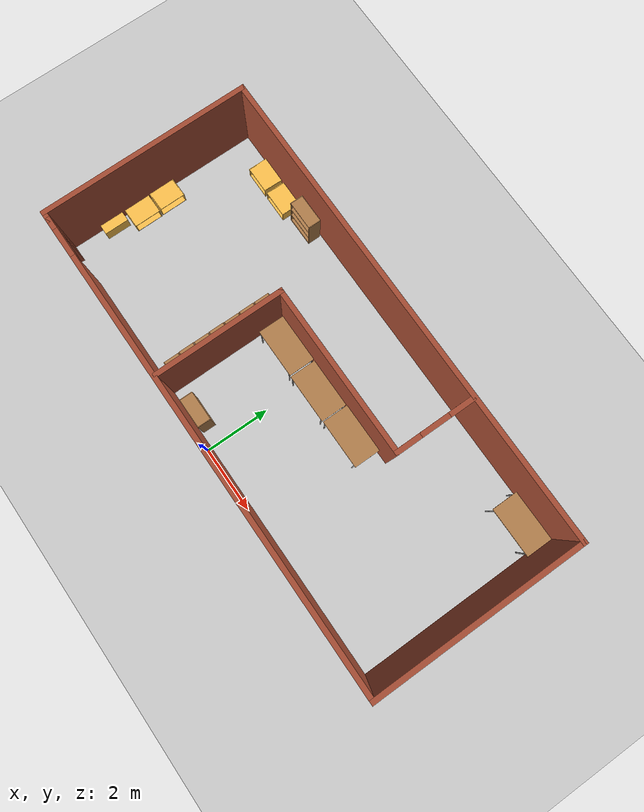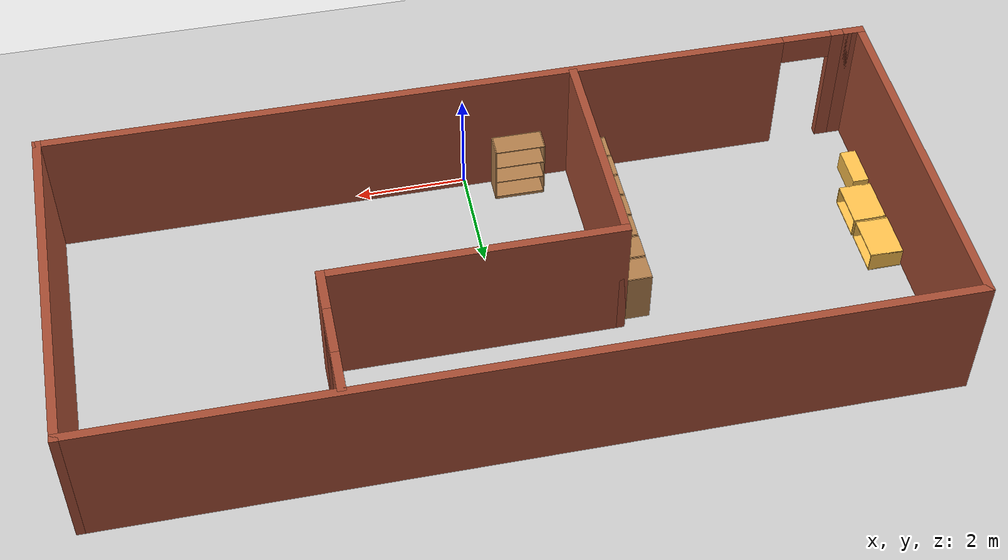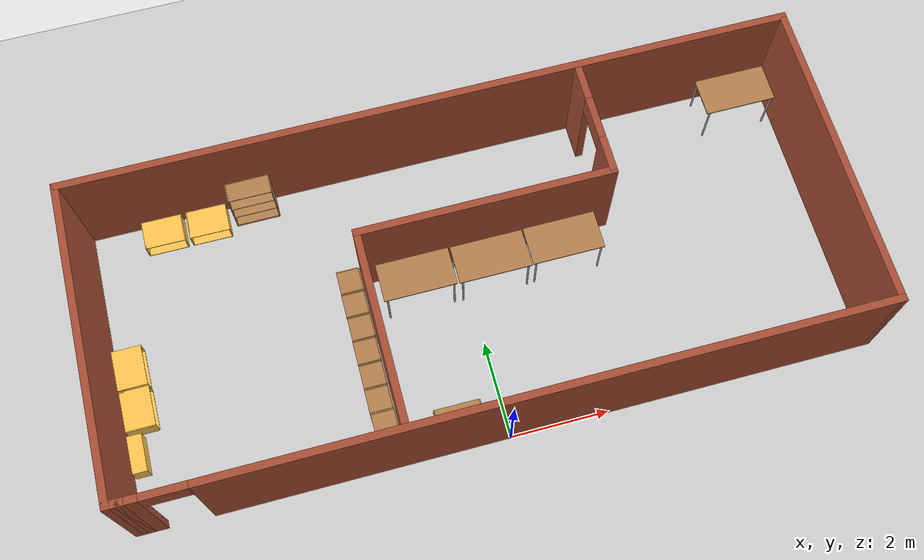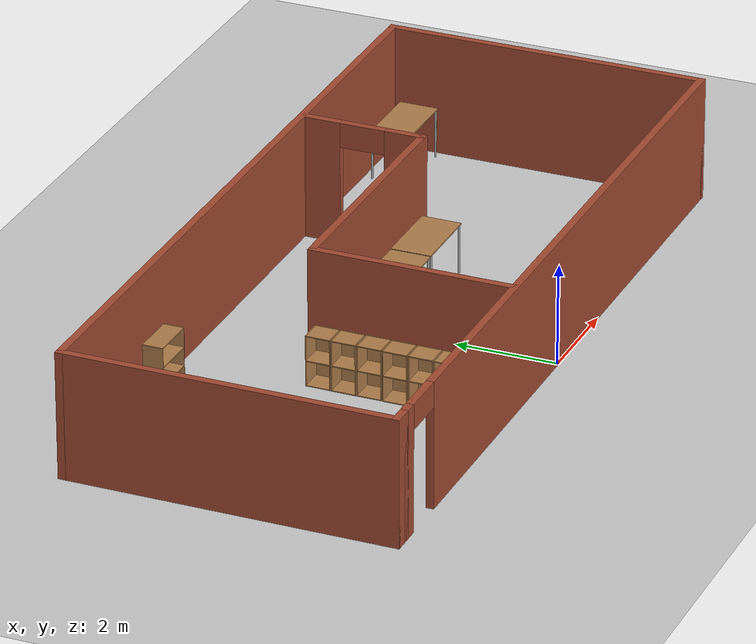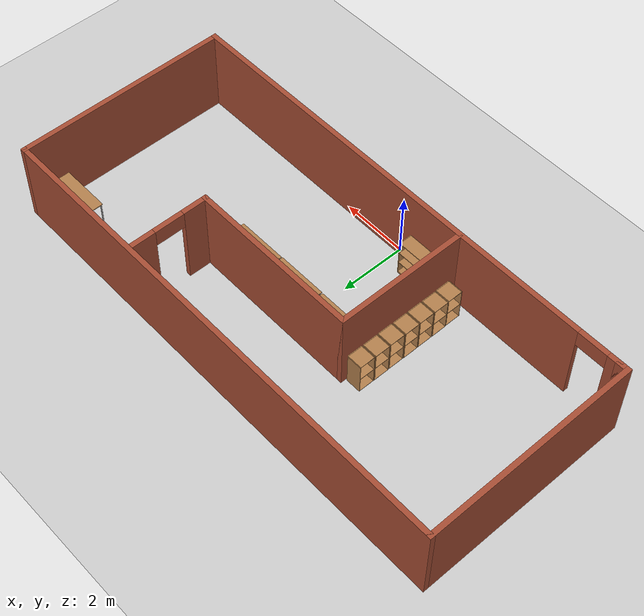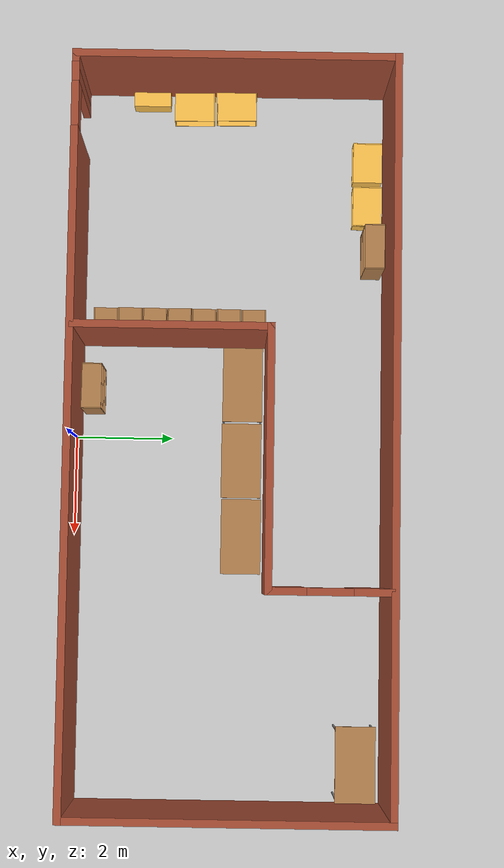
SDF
<sdf version="1.7">
 <world name="default">
  <light name="sun" type="directional">
   <pose>0 0 10 0 -0 0</pose>
   <diffuse>0.8 0.8 0.8 1</diffuse>
   <specular>0.2 0.2 0.2 1</specular>
   <attenuation>
    <range>1000</range>
    <constant>0.9</constant>
    <linear>0.01</linear>
    <quadratic>0.001</quadratic>
   </attenuation>
   <direction>-0.5 0.1 -0.9</direction>
   <spot><inner_angle>0</inner_angle><outer_angle>0</outer_angle><falloff>0</falloff></spot>
  </light>
  <model name="ground_plane">
   <pose>0 0 0 0 -0 1</pose>
   <static>1</static>
   <link name="link">
    <collision name="collision">
     <geometry><plane><normal>0 0 1</normal><size>100 100</size></plane></geometry>
     <surface>
      <contact><collide_bitmask>65535</collide_bitmask></contact>
      <friction><ode><mu>100</mu><mu2>50</mu2></ode></friction>
     </surface>
    </collision>
    <visual name="visual">
     <cast_shadows>0</cast_shadows>
     <geometry><plane><normal>0 0 1</normal><size>100 100</size></plane></geometry>
     <material>
      <script><uri>file://media/materials/scripts/gazebo.material</uri><name>Gazebo/Grey</name></script>
     </material>
    </visual>
   </link>
  </model>
  <gravity>0 0 -9.8</gravity>
  <magnetic_field>6e-06 2.3e-05 -4.2e-05</magnetic_field>
  <atmosphere type="adiabatic"/>
  <physics type="ode">
   <max_step_size>0.001</max_step_size>
   <real_time_factor>1</real_time_factor>
   <real_time_update_rate>1000</real_time_update_rate>
  </physics>
  <scene><ambient>0.4 0.4 0.4 1</ambient><background>0.7 0.7 0.7 1</background><shadows>1</shadows></scene>
  <audio><device>default</device></audio>
  <spherical_coordinates>
   <surface_model>EARTH_WGS84</surface_model>
   <latitude_deg>0</latitude_deg>
   <longitude_deg>0</longitude_deg>
   <elevation>0</elevation>
   <heading_deg>0</heading_deg>
  </spherical_coordinates>
  <model name="Box_15x30">
   <link name="Wall">
    <pose>0 0 0.1985 0 -0 0</pose>
    <inertial>
     <mass>5</mass>
     <inertia><ixx>0.3089</ixx><iyy>0.1022</iyy><izz>0.2797</izz><ixy>0</ixy><ixz>0</ixz><iyz>0</iyz></inertia>
    </inertial>
    <collision name="Wall_Collision"><geometry><box><size>0.296 0.764 0.397</size></box></geometry></collision>
    <visual name="Wall_Visual">
     <geometry><box><size>0.296 0.764 0.397</size></box></geometry>
     <material>
      <script><uri>file://media/materials/scripts/gazebo.material</uri><name>Gazebo/Grey</name></script>
      <ambient>1 0.764706 0.305882 1</ambient>
     </material>
    </visual>
   </link>
   <static>1</static>
   <pose>-7.11624 1.46432 0 0 -0 0</pose>
  </model>
  <model name="Fridge_Cabinet_33x15">
   <link name="Wall_17">
    <pose>0 0 0.01 0 -0 0</pose>
    <inertial>
     <mass>4.8627</mass>
     <inertia><ixx>0.146</ixx><iyy>0.4318</iyy><izz>0.2861</izz><ixy>0</ixy><ixz>0</ixz><iyz>0</iyz></inertia>
    </inertial>
    <collision name="Wall_17_Collision"><geometry><box><size>0.84 0.6 0.02</size></box></geometry></collision>
    <visual name="Wall_17_Visual">
     <geometry><box><size>0.84 0.6 0.02</size></box></geometry>
     <material>
      <script><uri>file://media/materials/scripts/gazebo.material</uri><name>Gazebo/Grey</name></script>
      <ambient>1 0.764706 0.305882 1</ambient>
     </material>
    </visual>
   </link>
   <joint name="17_21" type="fixed">
    <pose>0.42 0 0 0 -0 0</pose>
    <parent>Wall_21</parent>
    <child>Wall_17</child>
    <axis><xyz>1 0 0</xyz><limit><lower>-1e+16</lower><upper>1e+16</upper></limit></axis>
   </joint>
   <joint name="17_19" type="fixed">
    <pose>-0.42 0 0 0 -0 0</pose>
    <parent>Wall_19</parent>
    <child>Wall_17</child>
    <axis><xyz>1 0 0</xyz><limit><lower>-1e+16</lower><upper>1e+16</upper></limit></axis>
   </joint>
   <joint name="17_25" type="fixed">
    <pose>0 -0.3 0 0 -0 0</pose>
    <parent>Wall_25</parent>
    <child>Wall_17</child>
    <axis><xyz>0 1 0</xyz><limit><lower>-1e+16</lower><upper>1e+16</upper></limit></axis>
   </joint>
   <link name="Wall_19">
    <pose>-0.41 0 0.192 0 -0 0</pose>
    <inertial>
     <mass>2.223</mass>
     <inertia><ixx>0.0668</ixx><iyy>0.094</iyy><izz>0.0274</izz><ixy>0</ixy><ixz>0</ixz><iyz>0</iyz></inertia>
    </inertial>
    <collision name="Wall_19_Collision"><geometry><box><size>0.02 0.6 0.384</size></box></geometry></collision>
    <visual name="Wall_19_Visual">
     <geometry><box><size>0.02 0.6 0.384</size></box></geometry>
     <material>
      <script><uri>file://media/materials/scripts/gazebo.material</uri><name>Gazebo/Grey</name></script>
      <ambient>1 0.764706 0.305882 1</ambient>
     </material>
    </visual>
   </link>
   <link name="Wall_21">
    <pose>0.41 0 0.192 0 -0 0</pose>
    <inertial>
     <mass>2.223</mass>
     <inertia><ixx>0.0668</ixx><iyy>0.094</iyy><izz>0.0274</izz><ixy>0</ixy><ixz>0</ixz><iyz>0</iyz></inertia>
    </inertial>
    <collision name="Wall_21_Collision"><geometry><box><size>0.02 0.6 0.384</size></box></geometry></collision>
    <visual name="Wall_21_Visual">
     <geometry><box><size>0.02 0.6 0.384</size></box></geometry>
     <material>
      <script><uri>file://media/materials/scripts/gazebo.material</uri><name>Gazebo/Grey</name></script>
      <ambient>1 0.764706 0.305882 1</ambient>
     </material>
    </visual>
   </link>
   <link name="Wall_23">
    <pose>0 0 0.374 0 -0 0</pose>
    <inertial>
     <mass>4.8627</mass>
     <inertia><ixx>0.146</ixx><iyy>0.4318</iyy><izz>0.2861</izz><ixy>0</ixy><ixz>0</ixz><iyz>0</iyz></inertia>
    </inertial>
    <collision name="Wall_23_Collision"><geometry><box><size>0.84 0.6 0.02</size></box></geometry></collision>
    <visual name="Wall_23_Visual">
     <geometry><box><size>0.84 0.6 0.02</size></box></geometry>
     <material>
      <script><uri>file://media/materials/scripts/gazebo.material</uri><name>Gazebo/Grey</name></script>
      <ambient>1 0.764706 0.305882 1</ambient>
     </material>
    </visual>
   </link>
   <joint name="23_21" type="fixed">
    <pose>0.42 0 0 0 -0 0</pose>
    <parent>Wall_21</parent>
    <child>Wall_23</child>
    <axis><xyz>0 0 1</xyz><limit><lower>-1e+16</lower><upper>1e+16</upper></limit></axis>
   </joint>
   <joint name="23_19" type="fixed">
    <pose>-0.42 0 0 0 -0 0</pose>
    <parent>Wall_19</parent>
    <child>Wall_23</child>
    <axis><xyz>0 0 1</xyz><limit><lower>-1e+16</lower><upper>1e+16</upper></limit></axis>
   </joint>
   <joint name="23_25" type="fixed">
    <pose>0 -0.3 0 0 -0 0</pose>
    <parent>Wall_25</parent>
    <child>Wall_23</child>
    <axis><xyz>0 0 1</xyz><limit><lower>-1e+16</lower><upper>1e+16</upper></limit></axis>
   </joint>
   <link name="Wall_25">
    <pose>0 -0.29 0.19 0 -0 0</pose>
    <inertial>
     <mass>3.0651</mass>
     <inertia><ixx>0.037</ixx><iyy>0.1786</iyy><izz>0.2154</izz><ixy>0</ixy><ixz>0</ixz><iyz>0</iyz></inertia>
    </inertial>
    <collision name="Wall_25_Collision"><geometry><box><size>0.836 0.02 0.38</size></box></geometry></collision>
    <visual name="Wall_25_Visual">
     <geometry><box><size>0.836 0.02 0.38</size></box></geometry>
     <material>
      <script><uri>file://media/materials/scripts/gazebo.material</uri><name>Gazebo/Grey</name></script>
      <ambient>1 0.764706 0.305882 1</ambient>
     </material>
    </visual>
   </link>
   <joint name="25_21" type="fixed">
    <pose>0.42 0 0 0 -0 0</pose>
    <parent>Wall_21</parent>
    <child>Wall_25</child>
    <axis><xyz>0 1 0</xyz><limit><lower>-1e+16</lower><upper>1e+16</upper></limit></axis>
   </joint>
   <joint name="25_19" type="fixed">
    <pose>-0.42 0 0 0 -0 0</pose>
    <parent>Wall_19</parent>
    <child>Wall_25</child>
    <axis><xyz>0 1 0</xyz><limit><lower>-1e+16</lower><upper>1e+16</upper></limit></axis>
   </joint>
   <static>1</static>
   <pose>-6.96819 2.35258 0 0 0 -1.56459</pose>
  </model>
  <model name="Fridge_Cabinet_33x15_clone">
   <link name="Wall_17">
    <pose>0 0 0.01 0 -0 0</pose>
    <inertial>
     <mass>4.8627</mass>
     <inertia><ixx>0.146</ixx><iyy>0.4318</iyy><izz>0.2861</izz><ixy>0</ixy><ixz>0</ixz><iyz>0</iyz></inertia>
    </inertial>
    <collision name="Wall_17_Collision"><geometry><box><size>0.84 0.6 0.02</size></box></geometry></collision>
    <visual name="Wall_17_Visual">
     <geometry><box><size>0.84 0.6 0.02</size></box></geometry>
     <material>
      <script><uri>file://media/materials/scripts/gazebo.material</uri><name>Gazebo/Grey</name></script>
      <ambient>1 0.764706 0.305882 1</ambient>
     </material>
    </visual>
   </link>
   <joint name="17_21" type="fixed">
    <pose>0.42 0 0 0 -0 0</pose>
    <parent>Wall_21</parent>
    <child>Wall_17</child>
    <axis><xyz>1 0 0</xyz><limit><lower>-1e+16</lower><upper>1e+16</upper></limit></axis>
   </joint>
   <joint name="17_19" type="fixed">
    <pose>-0.42 0 0 0 -0 0</pose>
    <parent>Wall_19</parent>
    <child>Wall_17</child>
    <axis><xyz>1 0 0</xyz><limit><lower>-1e+16</lower><upper>1e+16</upper></limit></axis>
   </joint>
   <joint name="17_25" type="fixed">
    <pose>0 -0.3 0 0 -0 0</pose>
    <parent>Wall_25</parent>
    <child>Wall_17</child>
    <axis><xyz>0 1 0</xyz><limit><lower>-1e+16</lower><upper>1e+16</upper></limit></axis>
   </joint>
   <link name="Wall_19">
    <pose>-0.41 0 0.192 0 -0 0</pose>
    <inertial>
     <mass>2.223</mass>
     <inertia><ixx>0.0668</ixx><iyy>0.094</iyy><izz>0.0274</izz><ixy>0</ixy><ixz>0</ixz><iyz>0</iyz></inertia>
    </inertial>
    <collision name="Wall_19_Collision"><geometry><box><size>0.02 0.6 0.384</size></box></geometry></collision>
    <visual name="Wall_19_Visual">
     <geometry><box><size>0.02 0.6 0.384</size></box></geometry>
     <material>
      <script><uri>file://media/materials/scripts/gazebo.material</uri><name>Gazebo/Grey</name></script>
      <ambient>1 0.764706 0.305882 1</ambient>
     </material>
    </visual>
   </link>
   <link name="Wall_21">
    <pose>0.41 0 0.192 0 -0 0</pose>
    <inertial>
     <mass>2.223</mass>
     <inertia><ixx>0.0668</ixx><iyy>0.094</iyy><izz>0.0274</izz><ixy>0</ixy><ixz>0</ixz><iyz>0</iyz></inertia>
    </inertial>
    <collision name="Wall_21_Collision"><geometry><box><size>0.02 0.6 0.384</size></box></geometry></collision>
    <visual name="Wall_21_Visual">
     <geometry><box><size>0.02 0.6 0.384</size></box></geometry>
     <material>
      <script><uri>file://media/materials/scripts/gazebo.material</uri><name>Gazebo/Grey</name></script>
      <ambient>1 0.764706 0.305882 1</ambient>
     </material>
    </visual>
   </link>
   <link name="Wall_23">
    <pose>0 0 0.374 0 -0 0</pose>
    <inertial>
     <mass>4.8627</mass>
     <inertia><ixx>0.146</ixx><iyy>0.4318</iyy><izz>0.2861</izz><ixy>0</ixy><ixz>0</ixz><iyz>0</iyz></inertia>
    </inertial>
    <collision name="Wall_23_Collision"><geometry><box><size>0.84 0.6 0.02</size></box></geometry></collision>
    <visual name="Wall_23_Visual">
     <geometry><box><size>0.84 0.6 0.02</size></box></geometry>
     <material>
      <script><uri>file://media/materials/scripts/gazebo.material</uri><name>Gazebo/Grey</name></script>
      <ambient>1 0.764706 0.305882 1</ambient>
     </material>
    </visual>
   </link>
   <joint name="23_21" type="fixed">
    <pose>0.42 0 0 0 -0 0</pose>
    <parent>Wall_21</parent>
    <child>Wall_23</child>
    <axis><xyz>0 0 1</xyz><limit><lower>-1e+16</lower><upper>1e+16</upper></limit></axis>
   </joint>
   <joint name="23_19" type="fixed">
    <pose>-0.42 0 0 0 -0 0</pose>
    <parent>Wall_19</parent>
    <child>Wall_23</child>
    <axis><xyz>0 0 1</xyz><limit><lower>-1e+16</lower><upper>1e+16</upper></limit></axis>
   </joint>
   <joint name="23_25" type="fixed">
    <pose>0 -0.3 0 0 -0 0</pose>
    <parent>Wall_25</parent>
    <child>Wall_23</child>
    <axis><xyz>0 0 1</xyz><limit><lower>-1e+16</lower><upper>1e+16</upper></limit></axis>
   </joint>
   <link name="Wall_25">
    <pose>0 -0.29 0.19 0 -0 0</pose>
    <inertial>
     <mass>3.0651</mass>
     <inertia><ixx>0.037</ixx><iyy>0.1786</iyy><izz>0.2154</izz><ixy>0</ixy><ixz>0</ixz><iyz>0</iyz></inertia>
    </inertial>
    <collision name="Wall_25_Collision"><geometry><box><size>0.836 0.02 0.38</size></box></geometry></collision>
    <visual name="Wall_25_Visual">
     <geometry><box><size>0.836 0.02 0.38</size></box></geometry>
     <material>
      <script><uri>file://media/materials/scripts/gazebo.material</uri><name>Gazebo/Grey</name></script>
      <ambient>1 0.764706 0.305882 1</ambient>
     </material>
    </visual>
   </link>
   <joint name="25_21" type="fixed">
    <pose>0.42 0 0 0 -0 0</pose>
    <parent>Wall_21</parent>
    <child>Wall_25</child>
    <axis><xyz>0 1 0</xyz><limit><lower>-1e+16</lower><upper>1e+16</upper></limit></axis>
   </joint>
   <joint name="25_19" type="fixed">
    <pose>-0.42 0 0 0 -0 0</pose>
    <parent>Wall_19</parent>
    <child>Wall_25</child>
    <axis><xyz>0 1 0</xyz><limit><lower>-1e+16</lower><upper>1e+16</upper></limit></axis>
   </joint>
   <static>1</static>
   <pose>-6.98599 3.22667 0 0 0 -1.56459</pose>
  </model>
  <model name="Fridge_Cabinet_33x15_clone_0">
   <link name="Wall_17">
    <pose>0 0 0.01 0 -0 0</pose>
    <inertial>
     <mass>4.8627</mass>
     <inertia><ixx>0.146</ixx><iyy>0.4318</iyy><izz>0.2861</izz><ixy>0</ixy><ixz>0</ixz><iyz>0</iyz></inertia>
    </inertial>
    <collision name="Wall_17_Collision"><geometry><box><size>0.84 0.6 0.02</size></box></geometry></collision>
    <visual name="Wall_17_Visual">
     <geometry><box><size>0.84 0.6 0.02</size></box></geometry>
     <material>
      <script><uri>file://media/materials/scripts/gazebo.material</uri><name>Gazebo/Grey</name></script>
      <ambient>1 0.764706 0.305882 1</ambient>
     </material>
    </visual>
   </link>
   <joint name="17_21" type="fixed">
    <pose>0.42 0 0 0 -0 0</pose>
    <parent>Wall_21</parent>
    <child>Wall_17</child>
    <axis><xyz>1 0 0</xyz><limit><lower>-1e+16</lower><upper>1e+16</upper></limit></axis>
   </joint>
   <joint name="17_19" type="fixed">
    <pose>-0.42 0 0 0 -0 0</pose>
    <parent>Wall_19</parent>
    <child>Wall_17</child>
    <axis><xyz>1 0 0</xyz><limit><lower>-1e+16</lower><upper>1e+16</upper></limit></axis>
   </joint>
   <joint name="17_25" type="fixed">
    <pose>0 -0.3 0 0 -0 0</pose>
    <parent>Wall_25</parent>
    <child>Wall_17</child>
    <axis><xyz>0 1 0</xyz><limit><lower>-1e+16</lower><upper>1e+16</upper></limit></axis>
   </joint>
   <link name="Wall_19">
    <pose>-0.41 0 0.192 0 -0 0</pose>
    <inertial>
     <mass>2.223</mass>
     <inertia><ixx>0.0668</ixx><iyy>0.094</iyy><izz>0.0274</izz><ixy>0</ixy><ixz>0</ixz><iyz>0</iyz></inertia>
    </inertial>
    <collision name="Wall_19_Collision"><geometry><box><size>0.02 0.6 0.384</size></box></geometry></collision>
    <visual name="Wall_19_Visual">
     <geometry><box><size>0.02 0.6 0.384</size></box></geometry>
     <material>
      <script><uri>file://media/materials/scripts/gazebo.material</uri><name>Gazebo/Grey</name></script>
      <ambient>1 0.764706 0.305882 1</ambient>
     </material>
    </visual>
   </link>
   <link name="Wall_21">
    <pose>0.41 0 0.192 0 -0 0</pose>
    <inertial>
     <mass>2.223</mass>
     <inertia><ixx>0.0668</ixx><iyy>0.094</iyy><izz>0.0274</izz><ixy>0</ixy><ixz>0</ixz><iyz>0</iyz></inertia>
    </inertial>
    <collision name="Wall_21_Collision"><geometry><box><size>0.02 0.6 0.384</size></box></geometry></collision>
    <visual name="Wall_21_Visual">
     <geometry><box><size>0.02 0.6 0.384</size></box></geometry>
     <material>
      <script><uri>file://media/materials/scripts/gazebo.material</uri><name>Gazebo/Grey</name></script>
      <ambient>1 0.764706 0.305882 1</ambient>
     </material>
    </visual>
   </link>
   <link name="Wall_23">
    <pose>0 0 0.374 0 -0 0</pose>
    <inertial>
     <mass>4.8627</mass>
     <inertia><ixx>0.146</ixx><iyy>0.4318</iyy><izz>0.2861</izz><ixy>0</ixy><ixz>0</ixz><iyz>0</iyz></inertia>
    </inertial>
    <collision name="Wall_23_Collision"><geometry><box><size>0.84 0.6 0.02</size></box></geometry></collision>
    <visual name="Wall_23_Visual">
     <geometry><box><size>0.84 0.6 0.02</size></box></geometry>
     <material>
      <script><uri>file://media/materials/scripts/gazebo.material</uri><name>Gazebo/Grey</name></script>
      <ambient>1 0.764706 0.305882 1</ambient>
     </material>
    </visual>
   </link>
   <joint name="23_21" type="fixed">
    <pose>0.42 0 0 0 -0 0</pose>
    <parent>Wall_21</parent>
    <child>Wall_23</child>
    <axis><xyz>0 0 1</xyz><limit><lower>-1e+16</lower><upper>1e+16</upper></limit></axis>
   </joint>
   <joint name="23_19" type="fixed">
    <pose>-0.42 0 0 0 -0 0</pose>
    <parent>Wall_19</parent>
    <child>Wall_23</child>
    <axis><xyz>0 0 1</xyz><limit><lower>-1e+16</lower><upper>1e+16</upper></limit></axis>
   </joint>
   <joint name="23_25" type="fixed">
    <pose>0 -0.3 0 0 -0 0</pose>
    <parent>Wall_25</parent>
    <child>Wall_23</child>
    <axis><xyz>0 0 1</xyz><limit><lower>-1e+16</lower><upper>1e+16</upper></limit></axis>
   </joint>
   <link name="Wall_25">
    <pose>0 -0.29 0.19 0 -0 0</pose>
    <inertial>
     <mass>3.0651</mass>
     <inertia><ixx>0.037</ixx><iyy>0.1786</iyy><izz>0.2154</izz><ixy>0</ixy><ixz>0</ixz><iyz>0</iyz></inertia>
    </inertial>
    <collision name="Wall_25_Collision"><geometry><box><size>0.836 0.02 0.38</size></box></geometry></collision>
    <visual name="Wall_25_Visual">
     <geometry><box><size>0.836 0.02 0.38</size></box></geometry>
     <material>
      <script><uri>file://media/materials/scripts/gazebo.material</uri><name>Gazebo/Grey</name></script>
      <ambient>1 0.764706 0.305882 1</ambient>
     </material>
    </visual>
   </link>
   <joint name="25_21" type="fixed">
    <pose>0.42 0 0 0 -0 0</pose>
    <parent>Wall_21</parent>
    <child>Wall_25</child>
    <axis><xyz>0 1 0</xyz><limit><lower>-1e+16</lower><upper>1e+16</upper></limit></axis>
   </joint>
   <joint name="25_19" type="fixed">
    <pose>-0.42 0 0 0 -0 0</pose>
    <parent>Wall_19</parent>
    <child>Wall_25</child>
    <axis><xyz>0 1 0</xyz><limit><lower>-1e+16</lower><upper>1e+16</upper></limit></axis>
   </joint>
   <static>1</static>
   <pose>-5.82805 5.98325 -0.002918 0 -0 3.13541</pose>
  </model>
  <model name="Fridge_Cabinet_33x15_clone_0_clone">
   <link name="Wall_17">
    <pose>0 0 0.01 0 -0 0</pose>
    <inertial>
     <mass>4.8627</mass>
     <inertia><ixx>0.146</ixx><iyy>0.4318</iyy><izz>0.2861</izz><ixy>0</ixy><ixz>0</ixz><iyz>0</iyz></inertia>
    </inertial>
    <collision name="Wall_17_Collision"><geometry><box><size>0.84 0.6 0.02</size></box></geometry></collision>
    <visual name="Wall_17_Visual">
     <geometry><box><size>0.84 0.6 0.02</size></box></geometry>
     <material>
      <script><uri>file://media/materials/scripts/gazebo.material</uri><name>Gazebo/Grey</name></script>
      <ambient>1 0.764706 0.305882 1</ambient>
     </material>
    </visual>
   </link>
   <joint name="17_21" type="fixed">
    <pose>0.42 0 0 0 -0 0</pose>
    <parent>Wall_21</parent>
    <child>Wall_17</child>
    <axis><xyz>1 0 0</xyz><limit><lower>-1e+16</lower><upper>1e+16</upper></limit></axis>
   </joint>
   <joint name="17_19" type="fixed">
    <pose>-0.42 0 0 0 -0 0</pose>
    <parent>Wall_19</parent>
    <child>Wall_17</child>
    <axis><xyz>1 0 0</xyz><limit><lower>-1e+16</lower><upper>1e+16</upper></limit></axis>
   </joint>
   <joint name="17_25" type="fixed">
    <pose>0 -0.3 0 0 -0 0</pose>
    <parent>Wall_25</parent>
    <child>Wall_17</child>
    <axis><xyz>0 1 0</xyz><limit><lower>-1e+16</lower><upper>1e+16</upper></limit></axis>
   </joint>
   <link name="Wall_19">
    <pose>-0.41 0 0.192 0 -0 0</pose>
    <inertial>
     <mass>2.223</mass>
     <inertia><ixx>0.0668</ixx><iyy>0.094</iyy><izz>0.0274</izz><ixy>0</ixy><ixz>0</ixz><iyz>0</iyz></inertia>
    </inertial>
    <collision name="Wall_19_Collision"><geometry><box><size>0.02 0.6 0.384</size></box></geometry></collision>
    <visual name="Wall_19_Visual">
     <geometry><box><size>0.02 0.6 0.384</size></box></geometry>
     <material>
      <script><uri>file://media/materials/scripts/gazebo.material</uri><name>Gazebo/Grey</name></script>
      <ambient>1 0.764706 0.305882 1</ambient>
     </material>
    </visual>
   </link>
   <link name="Wall_21">
    <pose>0.41 0 0.192 0 -0 0</pose>
    <inertial>
     <mass>2.223</mass>
     <inertia><ixx>0.0668</ixx><iyy>0.094</iyy><izz>0.0274</izz><ixy>0</ixy><ixz>0</ixz><iyz>0</iyz></inertia>
    </inertial>
    <collision name="Wall_21_Collision"><geometry><box><size>0.02 0.6 0.384</size></box></geometry></collision>
    <visual name="Wall_21_Visual">
     <geometry><box><size>0.02 0.6 0.384</size></box></geometry>
     <material>
      <script><uri>file://media/materials/scripts/gazebo.material</uri><name>Gazebo/Grey</name></script>
      <ambient>1 0.764706 0.305882 1</ambient>
     </material>
    </visual>
   </link>
   <link name="Wall_23">
    <pose>0 0 0.374 0 -0 0</pose>
    <inertial>
     <mass>4.8627</mass>
     <inertia><ixx>0.146</ixx><iyy>0.4318</iyy><izz>0.2861</izz><ixy>0</ixy><ixz>0</ixz><iyz>0</iyz></inertia>
    </inertial>
    <collision name="Wall_23_Collision"><geometry><box><size>0.84 0.6 0.02</size></box></geometry></collision>
    <visual name="Wall_23_Visual">
     <geometry><box><size>0.84 0.6 0.02</size></box></geometry>
     <material>
      <script><uri>file://media/materials/scripts/gazebo.material</uri><name>Gazebo/Grey</name></script>
      <ambient>1 0.764706 0.305882 1</ambient>
     </material>
    </visual>
   </link>
   <joint name="23_21" type="fixed">
    <pose>0.42 0 0 0 -0 0</pose>
    <parent>Wall_21</parent>
    <child>Wall_23</child>
    <axis><xyz>0 0 1</xyz><limit><lower>-1e+16</lower><upper>1e+16</upper></limit></axis>
   </joint>
   <joint name="23_19" type="fixed">
    <pose>-0.42 0 0 0 -0 0</pose>
    <parent>Wall_19</parent>
    <child>Wall_23</child>
    <axis><xyz>0 0 1</xyz><limit><lower>-1e+16</lower><upper>1e+16</upper></limit></axis>
   </joint>
   <joint name="23_25" type="fixed">
    <pose>0 -0.3 0 0 -0 0</pose>
    <parent>Wall_25</parent>
    <child>Wall_23</child>
    <axis><xyz>0 0 1</xyz><limit><lower>-1e+16</lower><upper>1e+16</upper></limit></axis>
   </joint>
   <link name="Wall_25">
    <pose>0 -0.29 0.19 0 -0 0</pose>
    <inertial>
     <mass>3.0651</mass>
     <inertia><ixx>0.037</ixx><iyy>0.1786</iyy><izz>0.2154</izz><ixy>0</ixy><ixz>0</ixz><iyz>0</iyz></inertia>
    </inertial>
    <collision name="Wall_25_Collision"><geometry><box><size>0.836 0.02 0.38</size></box></geometry></collision>
    <visual name="Wall_25_Visual">
     <geometry><box><size>0.836 0.02 0.38</size></box></geometry>
     <material>
      <script><uri>file://media/materials/scripts/gazebo.material</uri><name>Gazebo/Grey</name></script>
      <ambient>1 0.764706 0.305882 1</ambient>
     </material>
    </visual>
   </link>
   <joint name="25_21" type="fixed">
    <pose>0.42 0 0 0 -0 0</pose>
    <parent>Wall_21</parent>
    <child>Wall_25</child>
    <axis><xyz>0 1 0</xyz><limit><lower>-1e+16</lower><upper>1e+16</upper></limit></axis>
   </joint>
   <joint name="25_19" type="fixed">
    <pose>-0.42 0 0 0 -0 0</pose>
    <parent>Wall_19</parent>
    <child>Wall_25</child>
    <axis><xyz>0 1 0</xyz><limit><lower>-1e+16</lower><upper>1e+16</upper></limit></axis>
   </joint>
   <static>1</static>
   <pose>-4.89868 5.98228 -0 0 -0 3.13541</pose>
  </model>
  <model name="cabinet">
   <static>1</static>
   <link name="cabinet_bottom_plate">
    <inertial>
     <pose>0 0 -1 0 -0 0</pose>
     <inertia><ixx>2.05</ixx><ixy>0</ixy><ixz>0</ixz><iyy>2.05</iyy><iyz>0</iyz><izz>2.05</izz></inertia>
     <mass>25</mass>
    </inertial>
    <collision name="cabinet_bottom_plate_geom">
     <pose>0 0 0.01 0 -0 0</pose>
     <geometry><box><size>0.45 0.45 0.02</size></box></geometry>
    </collision>
    <visual name="cabinet_bottom_plate_geom_visual">
     <pose>0 0 0.01 0 -0 0</pose>
     <geometry><box><size>0.45 0.45 0.02</size></box></geometry>
     <material>
      <script><uri>file://media/materials/scripts/gazebo.material</uri><name>Gazebo/Wood</name></script>
     </material>
    </visual>
    <collision name="cabinet_bottom_plate_geom_cabinet_back_plate">
     <pose>0.235 0 0.51 0 -0 0</pose>
     <geometry><box><size>0.02 0.45 1.02</size></box></geometry>
    </collision>
    <visual name="cabinet_bottom_plate_geom_cabinet_back_plate_visual">
     <pose>0.235 0 0.51 0 -0 0</pose>
     <geometry><box><size>0.02 0.45 1.02</size></box></geometry>
     <material>
      <script><uri>file://media/materials/scripts/gazebo.material</uri><name>Gazebo/Wood</name></script>
     </material>
    </visual>
    <collision name="cabinet_bottom_plate_geom_cabinet_left_plate">
     <pose>0 0.235 0.51 0 -0 0</pose>
     <geometry><box><size>0.45 0.02 1.02</size></box></geometry>
    </collision>
    <visual name="cabinet_bottom_plate_geom_cabinet_left_plate_visual">
     <pose>0 0.235 0.51 0 -0 0</pose>
     <geometry><box><size>0.45 0.02 1.02</size></box></geometry>
     <material>
      <script><uri>file://media/materials/scripts/gazebo.material</uri><name>Gazebo/Wood</name></script>
     </material>
    </visual>
    <collision name="cabinet_bottom_plate_geom_cabinet_middle_plate">
     <pose>0 0 0.51 0 -0 0</pose>
     <geometry><box><size>0.45 0.45 0.02</size></box></geometry>
    </collision>
    <visual name="cabinet_bottom_plate_geom_cabinet_middle_plate_visual">
     <pose>0 0 0.51 0 -0 0</pose>
     <geometry><box><size>0.45 0.45 0.02</size></box></geometry>
     <material>
      <script><uri>file://media/materials/scripts/gazebo.material</uri><name>Gazebo/Wood</name></script>
     </material>
    </visual>
    <collision name="cabinet_bottom_plate_geom_cabinet_right_plate">
     <pose>0 -0.235 0.51 0 -0 0</pose>
     <geometry><box><size>0.45 0.02 1.02</size></box></geometry>
    </collision>
    <visual name="cabinet_bottom_plate_geom_cabinet_right_plate_visual">
     <pose>0 -0.235 0.51 0 -0 0</pose>
     <geometry><box><size>0.45 0.02 1.02</size></box></geometry>
     <material>
      <script><uri>file://media/materials/scripts/gazebo.material</uri><name>Gazebo/Wood</name></script>
     </material>
    </visual>
    <collision name="cabinet_bottom_plate_geom_cabinet_top_plate">
     <pose>0 0 1.01 0 -0 0</pose>
     <geometry><box><size>0.45 0.45 0.02</size></box></geometry>
    </collision>
    <visual name="cabinet_bottom_plate_geom_cabinet_top_plate_visual">
     <pose>0 0 1.01 0 -0 0</pose>
     <geometry><box><size>0.45 0.45 0.02</size></box></geometry>
     <material>
      <script><uri>file://media/materials/scripts/gazebo.material</uri><name>Gazebo/Wood</name></script>
     </material>
    </visual>
   </link>
   <pose>-2.34318 3.63904 0 0 -0 0</pose>
  </model>
  <model name="cabinet_clone">
   <static>1</static>
   <link name="cabinet_bottom_plate">
    <inertial>
     <pose>0 0 -1 0 -0 0</pose>
     <inertia><ixx>2.05</ixx><ixy>0</ixy><ixz>0</ixz><iyy>2.05</iyy><iyz>0</iyz><izz>2.05</izz></inertia>
     <mass>25</mass>
    </inertial>
    <collision name="cabinet_bottom_plate_geom">
     <pose>0 0 0.01 0 -0 0</pose>
     <geometry><box><size>0.45 0.45 0.02</size></box></geometry>
    </collision>
    <visual name="cabinet_bottom_plate_geom_visual">
     <pose>0 0 0.01 0 -0 0</pose>
     <geometry><box><size>0.45 0.45 0.02</size></box></geometry>
     <material>
      <script><uri>file://media/materials/scripts/gazebo.material</uri><name>Gazebo/Wood</name></script>
     </material>
    </visual>
    <collision name="cabinet_bottom_plate_geom_cabinet_back_plate">
     <pose>0.235 0 0.51 0 -0 0</pose>
     <geometry><box><size>0.02 0.45 1.02</size></box></geometry>
    </collision>
    <visual name="cabinet_bottom_plate_geom_cabinet_back_plate_visual">
     <pose>0.235 0 0.51 0 -0 0</pose>
     <geometry><box><size>0.02 0.45 1.02</size></box></geometry>
     <material>
      <script><uri>file://media/materials/scripts/gazebo.material</uri><name>Gazebo/Wood</name></script>
     </material>
    </visual>
    <collision name="cabinet_bottom_plate_geom_cabinet_left_plate">
     <pose>0 0.235 0.51 0 -0 0</pose>
     <geometry><box><size>0.45 0.02 1.02</size></box></geometry>
    </collision>
    <visual name="cabinet_bottom_plate_geom_cabinet_left_plate_visual">
     <pose>0 0.235 0.51 0 -0 0</pose>
     <geometry><box><size>0.45 0.02 1.02</size></box></geometry>
     <material>
      <script><uri>file://media/materials/scripts/gazebo.material</uri><name>Gazebo/Wood</name></script>
     </material>
    </visual>
    <collision name="cabinet_bottom_plate_geom_cabinet_middle_plate">
     <pose>0 0 0.51 0 -0 0</pose>
     <geometry><box><size>0.45 0.45 0.02</size></box></geometry>
    </collision>
    <visual name="cabinet_bottom_plate_geom_cabinet_middle_plate_visual">
     <pose>0 0 0.51 0 -0 0</pose>
     <geometry><box><size>0.45 0.45 0.02</size></box></geometry>
     <material>
      <script><uri>file://media/materials/scripts/gazebo.material</uri><name>Gazebo/Wood</name></script>
     </material>
    </visual>
    <collision name="cabinet_bottom_plate_geom_cabinet_right_plate">
     <pose>0 -0.235 0.51 0 -0 0</pose>
     <geometry><box><size>0.45 0.02 1.02</size></box></geometry>
    </collision>
    <visual name="cabinet_bottom_plate_geom_cabinet_right_plate_visual">
     <pose>0 -0.235 0.51 0 -0 0</pose>
     <geometry><box><size>0.45 0.02 1.02</size></box></geometry>
     <material>
      <script><uri>file://media/materials/scripts/gazebo.material</uri><name>Gazebo/Wood</name></script>
     </material>
    </visual>
    <collision name="cabinet_bottom_plate_geom_cabinet_top_plate">
     <pose>0 0 1.01 0 -0 0</pose>
     <geometry><box><size>0.45 0.45 0.02</size></box></geometry>
    </collision>
    <visual name="cabinet_bottom_plate_geom_cabinet_top_plate_visual">
     <pose>0 0 1.01 0 -0 0</pose>
     <geometry><box><size>0.45 0.45 0.02</size></box></geometry>
     <material>
      <script><uri>file://media/materials/scripts/gazebo.material</uri><name>Gazebo/Wood</name></script>
     </material>
    </visual>
   </link>
   <pose>-2.34868 3.13711 0 0 -0 0</pose>
  </model>
  <model name="cabinet_clone_0">
   <static>1</static>
   <link name="cabinet_bottom_plate">
    <inertial>
     <pose>0 0 -1 0 -0 0</pose>
     <inertia><ixx>2.05</ixx><ixy>0</ixy><ixz>0</ixz><iyy>2.05</iyy><iyz>0</iyz><izz>2.05</izz></inertia>
     <mass>25</mass>
    </inertial>
    <collision name="cabinet_bottom_plate_geom">
     <pose>0 0 0.01 0 -0 0</pose>
     <geometry><box><size>0.45 0.45 0.02</size></box></geometry>
    </collision>
    <visual name="cabinet_bottom_plate_geom_visual">
     <pose>0 0 0.01 0 -0 0</pose>
     <geometry><box><size>0.45 0.45 0.02</size></box></geometry>
     <material>
      <script><uri>file://media/materials/scripts/gazebo.material</uri><name>Gazebo/Wood</name></script>
     </material>
    </visual>
    <collision name="cabinet_bottom_plate_geom_cabinet_back_plate">
     <pose>0.235 0 0.51 0 -0 0</pose>
     <geometry><box><size>0.02 0.45 1.02</size></box></geometry>
    </collision>
    <visual name="cabinet_bottom_plate_geom_cabinet_back_plate_visual">
     <pose>0.235 0 0.51 0 -0 0</pose>
     <geometry><box><size>0.02 0.45 1.02</size></box></geometry>
     <material>
      <script><uri>file://media/materials/scripts/gazebo.material</uri><name>Gazebo/Wood</name></script>
     </material>
    </visual>
    <collision name="cabinet_bottom_plate_geom_cabinet_left_plate">
     <pose>0 0.235 0.51 0 -0 0</pose>
     <geometry><box><size>0.45 0.02 1.02</size></box></geometry>
    </collision>
    <visual name="cabinet_bottom_plate_geom_cabinet_left_plate_visual">
     <pose>0 0.235 0.51 0 -0 0</pose>
     <geometry><box><size>0.45 0.02 1.02</size></box></geometry>
     <material>
      <script><uri>file://media/materials/scripts/gazebo.material</uri><name>Gazebo/Wood</name></script>
     </material>
    </visual>
    <collision name="cabinet_bottom_plate_geom_cabinet_middle_plate">
     <pose>0 0 0.51 0 -0 0</pose>
     <geometry><box><size>0.45 0.45 0.02</size></box></geometry>
    </collision>
    <visual name="cabinet_bottom_plate_geom_cabinet_middle_plate_visual">
     <pose>0 0 0.51 0 -0 0</pose>
     <geometry><box><size>0.45 0.45 0.02</size></box></geometry>
     <material>
      <script><uri>file://media/materials/scripts/gazebo.material</uri><name>Gazebo/Wood</name></script>
     </material>
    </visual>
    <collision name="cabinet_bottom_plate_geom_cabinet_right_plate">
     <pose>0 -0.235 0.51 0 -0 0</pose>
     <geometry><box><size>0.45 0.02 1.02</size></box></geometry>
    </collision>
    <visual name="cabinet_bottom_plate_geom_cabinet_right_plate_visual">
     <pose>0 -0.235 0.51 0 -0 0</pose>
     <geometry><box><size>0.45 0.02 1.02</size></box></geometry>
     <material>
      <script><uri>file://media/materials/scripts/gazebo.material</uri><name>Gazebo/Wood</name></script>
     </material>
    </visual>
    <collision name="cabinet_bottom_plate_geom_cabinet_top_plate">
     <pose>0 0 1.01 0 -0 0</pose>
     <geometry><box><size>0.45 0.45 0.02</size></box></geometry>
    </collision>
    <visual name="cabinet_bottom_plate_geom_cabinet_top_plate_visual">
     <pose>0 0 1.01 0 -0 0</pose>
     <geometry><box><size>0.45 0.45 0.02</size></box></geometry>
     <material>
      <script><uri>file://media/materials/scripts/gazebo.material</uri><name>Gazebo/Wood</name></script>
     </material>
    </visual>
   </link>
   <pose>-2.34547 2.63327 0 0 -0 0</pose>
  </model>
  <model name="cabinet_clone_1">
   <static>1</static>
   <link name="cabinet_bottom_plate">
    <inertial>
     <pose>0 0 -1 0 -0 0</pose>
     <inertia><ixx>2.05</ixx><ixy>0</ixy><ixz>0</ixz><iyy>2.05</iyy><iyz>0</iyz><izz>2.05</izz></inertia>
     <mass>25</mass>
    </inertial>
    <collision name="cabinet_bottom_plate_geom">
     <pose>0 0 0.01 0 -0 0</pose>
     <geometry><box><size>0.45 0.45 0.02</size></box></geometry>
    </collision>
    <visual name="cabinet_bottom_plate_geom_visual">
     <pose>0 0 0.01 0 -0 0</pose>
     <geometry><box><size>0.45 0.45 0.02</size></box></geometry>
     <material>
      <script><uri>file://media/materials/scripts/gazebo.material</uri><name>Gazebo/Wood</name></script>
     </material>
    </visual>
    <collision name="cabinet_bottom_plate_geom_cabinet_back_plate">
     <pose>0.235 0 0.51 0 -0 0</pose>
     <geometry><box><size>0.02 0.45 1.02</size></box></geometry>
    </collision>
    <visual name="cabinet_bottom_plate_geom_cabinet_back_plate_visual">
     <pose>0.235 0 0.51 0 -0 0</pose>
     <geometry><box><size>0.02 0.45 1.02</size></box></geometry>
     <material>
      <script><uri>file://media/materials/scripts/gazebo.material</uri><name>Gazebo/Wood</name></script>
     </material>
    </visual>
    <collision name="cabinet_bottom_plate_geom_cabinet_left_plate">
     <pose>0 0.235 0.51 0 -0 0</pose>
     <geometry><box><size>0.45 0.02 1.02</size></box></geometry>
    </collision>
    <visual name="cabinet_bottom_plate_geom_cabinet_left_plate_visual">
     <pose>0 0.235 0.51 0 -0 0</pose>
     <geometry><box><size>0.45 0.02 1.02</size></box></geometry>
     <material>
      <script><uri>file://media/materials/scripts/gazebo.material</uri><name>Gazebo/Wood</name></script>
     </material>
    </visual>
    <collision name="cabinet_bottom_plate_geom_cabinet_middle_plate">
     <pose>0 0 0.51 0 -0 0</pose>
     <geometry><box><size>0.45 0.45 0.02</size></box></geometry>
    </collision>
    <visual name="cabinet_bottom_plate_geom_cabinet_middle_plate_visual">
     <pose>0 0 0.51 0 -0 0</pose>
     <geometry><box><size>0.45 0.45 0.02</size></box></geometry>
     <material>
      <script><uri>file://media/materials/scripts/gazebo.material</uri><name>Gazebo/Wood</name></script>
     </material>
    </visual>
    <collision name="cabinet_bottom_plate_geom_cabinet_right_plate">
     <pose>0 -0.235 0.51 0 -0 0</pose>
     <geometry><box><size>0.45 0.02 1.02</size></box></geometry>
    </collision>
    <visual name="cabinet_bottom_plate_geom_cabinet_right_plate_visual">
     <pose>0 -0.235 0.51 0 -0 0</pose>
     <geometry><box><size>0.45 0.02 1.02</size></box></geometry>
     <material>
      <script><uri>file://media/materials/scripts/gazebo.material</uri><name>Gazebo/Wood</name></script>
     </material>
    </visual>
    <collision name="cabinet_bottom_plate_geom_cabinet_top_plate">
     <pose>0 0 1.01 0 -0 0</pose>
     <geometry><box><size>0.45 0.45 0.02</size></box></geometry>
    </collision>
    <visual name="cabinet_bottom_plate_geom_cabinet_top_plate_visual">
     <pose>0 0 1.01 0 -0 0</pose>
     <geometry><box><size>0.45 0.45 0.02</size></box></geometry>
     <material>
      <script><uri>file://media/materials/scripts/gazebo.material</uri><name>Gazebo/Wood</name></script>
     </material>
    </visual>
   </link>
   <pose>-2.35252 2.13202 0 0 -0 0</pose>
  </model>
  <model name="cabinet_clone_2">
   <static>1</static>
   <link name="cabinet_bottom_plate">
    <inertial>
     <pose>0 0 -1 0 -0 0</pose>
     <inertia><ixx>2.05</ixx><ixy>0</ixy><ixz>0</ixz><iyy>2.05</iyy><iyz>0</iyz><izz>2.05</izz></inertia>
     <mass>25</mass>
    </inertial>
    <collision name="cabinet_bottom_plate_geom">
     <pose>0 0 0.01 0 -0 0</pose>
     <geometry><box><size>0.45 0.45 0.02</size></box></geometry>
    </collision>
    <visual name="cabinet_bottom_plate_geom_visual">
     <pose>0 0 0.01 0 -0 0</pose>
     <geometry><box><size>0.45 0.45 0.02</size></box></geometry>
     <material>
      <script><uri>file://media/materials/scripts/gazebo.material</uri><name>Gazebo/Wood</name></script>
     </material>
    </visual>
    <collision name="cabinet_bottom_plate_geom_cabinet_back_plate">
     <pose>0.235 0 0.51 0 -0 0</pose>
     <geometry><box><size>0.02 0.45 1.02</size></box></geometry>
    </collision>
    <visual name="cabinet_bottom_plate_geom_cabinet_back_plate_visual">
     <pose>0.235 0 0.51 0 -0 0</pose>
     <geometry><box><size>0.02 0.45 1.02</size></box></geometry>
     <material>
      <script><uri>file://media/materials/scripts/gazebo.material</uri><name>Gazebo/Wood</name></script>
     </material>
    </visual>
    <collision name="cabinet_bottom_plate_geom_cabinet_left_plate">
     <pose>0 0.235 0.51 0 -0 0</pose>
     <geometry><box><size>0.45 0.02 1.02</size></box></geometry>
    </collision>
    <visual name="cabinet_bottom_plate_geom_cabinet_left_plate_visual">
     <pose>0 0.235 0.51 0 -0 0</pose>
     <geometry><box><size>0.45 0.02 1.02</size></box></geometry>
     <material>
      <script><uri>file://media/materials/scripts/gazebo.material</uri><name>Gazebo/Wood</name></script>
     </material>
    </visual>
    <collision name="cabinet_bottom_plate_geom_cabinet_middle_plate">
     <pose>0 0 0.51 0 -0 0</pose>
     <geometry><box><size>0.45 0.45 0.02</size></box></geometry>
    </collision>
    <visual name="cabinet_bottom_plate_geom_cabinet_middle_plate_visual">
     <pose>0 0 0.51 0 -0 0</pose>
     <geometry><box><size>0.45 0.45 0.02</size></box></geometry>
     <material>
      <script><uri>file://media/materials/scripts/gazebo.material</uri><name>Gazebo/Wood</name></script>
     </material>
    </visual>
    <collision name="cabinet_bottom_plate_geom_cabinet_right_plate">
     <pose>0 -0.235 0.51 0 -0 0</pose>
     <geometry><box><size>0.45 0.02 1.02</size></box></geometry>
    </collision>
    <visual name="cabinet_bottom_plate_geom_cabinet_right_plate_visual">
     <pose>0 -0.235 0.51 0 -0 0</pose>
     <geometry><box><size>0.45 0.02 1.02</size></box></geometry>
     <material>
      <script><uri>file://media/materials/scripts/gazebo.material</uri><name>Gazebo/Wood</name></script>
     </material>
    </visual>
    <collision name="cabinet_bottom_plate_geom_cabinet_top_plate">
     <pose>0 0 1.01 0 -0 0</pose>
     <geometry><box><size>0.45 0.45 0.02</size></box></geometry>
    </collision>
    <visual name="cabinet_bottom_plate_geom_cabinet_top_plate_visual">
     <pose>0 0 1.01 0 -0 0</pose>
     <geometry><box><size>0.45 0.45 0.02</size></box></geometry>
     <material>
      <script><uri>file://media/materials/scripts/gazebo.material</uri><name>Gazebo/Wood</name></script>
     </material>
    </visual>
   </link>
   <pose>-2.35147 1.62966 0 0 -0 0</pose>
  </model>
  <model name="cabinet_clone_3">
   <static>1</static>
   <link name="cabinet_bottom_plate">
    <inertial>
     <pose>0 0 -1 0 -0 0</pose>
     <inertia><ixx>2.05</ixx><ixy>0</ixy><ixz>0</ixz><iyy>2.05</iyy><iyz>0</iyz><izz>2.05</izz></inertia>
     <mass>25</mass>
    </inertial>
    <collision name="cabinet_bottom_plate_geom">
     <pose>0 0 0.01 0 -0 0</pose>
     <geometry><box><size>0.45 0.45 0.02</size></box></geometry>
    </collision>
    <visual name="cabinet_bottom_plate_geom_visual">
     <pose>0 0 0.01 0 -0 0</pose>
     <geometry><box><size>0.45 0.45 0.02</size></box></geometry>
     <material>
      <script><uri>file://media/materials/scripts/gazebo.material</uri><name>Gazebo/Wood</name></script>
     </material>
    </visual>
    <collision name="cabinet_bottom_plate_geom_cabinet_back_plate">
     <pose>0.235 0 0.51 0 -0 0</pose>
     <geometry><box><size>0.02 0.45 1.02</size></box></geometry>
    </collision>
    <visual name="cabinet_bottom_plate_geom_cabinet_back_plate_visual">
     <pose>0.235 0 0.51 0 -0 0</pose>
     <geometry><box><size>0.02 0.45 1.02</size></box></geometry>
     <material>
      <script><uri>file://media/materials/scripts/gazebo.material</uri><name>Gazebo/Wood</name></script>
     </material>
    </visual>
    <collision name="cabinet_bottom_plate_geom_cabinet_left_plate">
     <pose>0 0.235 0.51 0 -0 0</pose>
     <geometry><box><size>0.45 0.02 1.02</size></box></geometry>
    </collision>
    <visual name="cabinet_bottom_plate_geom_cabinet_left_plate_visual">
     <pose>0 0.235 0.51 0 -0 0</pose>
     <geometry><box><size>0.45 0.02 1.02</size></box></geometry>
     <material>
      <script><uri>file://media/materials/scripts/gazebo.material</uri><name>Gazebo/Wood</name></script>
     </material>
    </visual>
    <collision name="cabinet_bottom_plate_geom_cabinet_middle_plate">
     <pose>0 0 0.51 0 -0 0</pose>
     <geometry><box><size>0.45 0.45 0.02</size></box></geometry>
    </collision>
    <visual name="cabinet_bottom_plate_geom_cabinet_middle_plate_visual">
     <pose>0 0 0.51 0 -0 0</pose>
     <geometry><box><size>0.45 0.45 0.02</size></box></geometry>
     <material>
      <script><uri>file://media/materials/scripts/gazebo.material</uri><name>Gazebo/Wood</name></script>
     </material>
    </visual>
    <collision name="cabinet_bottom_plate_geom_cabinet_right_plate">
     <pose>0 -0.235 0.51 0 -0 0</pose>
     <geometry><box><size>0.45 0.02 1.02</size></box></geometry>
    </collision>
    <visual name="cabinet_bottom_plate_geom_cabinet_right_plate_visual">
     <pose>0 -0.235 0.51 0 -0 0</pose>
     <geometry><box><size>0.45 0.02 1.02</size></box></geometry>
     <material>
      <script><uri>file://media/materials/scripts/gazebo.material</uri><name>Gazebo/Wood</name></script>
     </material>
    </visual>
    <collision name="cabinet_bottom_plate_geom_cabinet_top_plate">
     <pose>0 0 1.01 0 -0 0</pose>
     <geometry><box><size>0.45 0.45 0.02</size></box></geometry>
    </collision>
    <visual name="cabinet_bottom_plate_geom_cabinet_top_plate_visual">
     <pose>0 0 1.01 0 -0 0</pose>
     <geometry><box><size>0.45 0.45 0.02</size></box></geometry>
     <material>
      <script><uri>file://media/materials/scripts/gazebo.material</uri><name>Gazebo/Wood</name></script>
     </material>
    </visual>
   </link>
   <pose>-2.35447 1.13007 0 0 -0 0</pose>
  </model>
  <model name="cabinet_clone_4">
   <static>1</static>
   <link name="cabinet_bottom_plate">
    <inertial>
     <pose>0 0 -1 0 -0 0</pose>
     <inertia><ixx>2.05</ixx><ixy>0</ixy><ixz>0</ixz><iyy>2.05</iyy><iyz>0</iyz><izz>2.05</izz></inertia>
     <mass>25</mass>
    </inertial>
    <collision name="cabinet_bottom_plate_geom">
     <pose>0 0 0.01 0 -0 0</pose>
     <geometry><box><size>0.45 0.45 0.02</size></box></geometry>
    </collision>
    <visual name="cabinet_bottom_plate_geom_visual">
     <pose>0 0 0.01 0 -0 0</pose>
     <geometry><box><size>0.45 0.45 0.02</size></box></geometry>
     <material>
      <script><uri>file://media/materials/scripts/gazebo.material</uri><name>Gazebo/Wood</name></script>
     </material>
    </visual>
    <collision name="cabinet_bottom_plate_geom_cabinet_back_plate">
     <pose>0.235 0 0.51 0 -0 0</pose>
     <geometry><box><size>0.02 0.45 1.02</size></box></geometry>
    </collision>
    <visual name="cabinet_bottom_plate_geom_cabinet_back_plate_visual">
     <pose>0.235 0 0.51 0 -0 0</pose>
     <geometry><box><size>0.02 0.45 1.02</size></box></geometry>
     <material>
      <script><uri>file://media/materials/scripts/gazebo.material</uri><name>Gazebo/Wood</name></script>
     </material>
    </visual>
    <collision name="cabinet_bottom_plate_geom_cabinet_left_plate">
     <pose>0 0.235 0.51 0 -0 0</pose>
     <geometry><box><size>0.45 0.02 1.02</size></box></geometry>
    </collision>
    <visual name="cabinet_bottom_plate_geom_cabinet_left_plate_visual">
     <pose>0 0.235 0.51 0 -0 0</pose>
     <geometry><box><size>0.45 0.02 1.02</size></box></geometry>
     <material>
      <script><uri>file://media/materials/scripts/gazebo.material</uri><name>Gazebo/Wood</name></script>
     </material>
    </visual>
    <collision name="cabinet_bottom_plate_geom_cabinet_middle_plate">
     <pose>0 0 0.51 0 -0 0</pose>
     <geometry><box><size>0.45 0.45 0.02</size></box></geometry>
    </collision>
    <visual name="cabinet_bottom_plate_geom_cabinet_middle_plate_visual">
     <pose>0 0 0.51 0 -0 0</pose>
     <geometry><box><size>0.45 0.45 0.02</size></box></geometry>
     <material>
      <script><uri>file://media/materials/scripts/gazebo.material</uri><name>Gazebo/Wood</name></script>
     </material>
    </visual>
    <collision name="cabinet_bottom_plate_geom_cabinet_right_plate">
     <pose>0 -0.235 0.51 0 -0 0</pose>
     <geometry><box><size>0.45 0.02 1.02</size></box></geometry>
    </collision>
    <visual name="cabinet_bottom_plate_geom_cabinet_right_plate_visual">
     <pose>0 -0.235 0.51 0 -0 0</pose>
     <geometry><box><size>0.45 0.02 1.02</size></box></geometry>
     <material>
      <script><uri>file://media/materials/scripts/gazebo.material</uri><name>Gazebo/Wood</name></script>
     </material>
    </visual>
    <collision name="cabinet_bottom_plate_geom_cabinet_top_plate">
     <pose>0 0 1.01 0 -0 0</pose>
     <geometry><box><size>0.45 0.45 0.02</size></box></geometry>
    </collision>
    <visual name="cabinet_bottom_plate_geom_cabinet_top_plate_visual">
     <pose>0 0 1.01 0 -0 0</pose>
     <geometry><box><size>0.45 0.45 0.02</size></box></geometry>
     <material>
      <script><uri>file://media/materials/scripts/gazebo.material</uri><name>Gazebo/Wood</name></script>
     </material>
    </visual>
   </link>
   <pose>-2.34562 0.634937 0 0 -0 0</pose>
  </model>
  <model name="bookshelf">
   <static>1</static>
   <link name="link">
    <inertial><mass>1</mass></inertial>
    <collision name="back">
     <pose>0 0.005 0.6 0 -0 0</pose>
     <geometry><box><size>0.9 0.01 1.2</size></box></geometry>
    </collision>
    <visual name="visual1">
     <pose>0 0.005 0.6 0 -0 0</pose>
     <geometry><box><size>0.9 0.01 1.2</size></box></geometry>
     <material>
      <script><uri>file://media/materials/scripts/gazebo.material</uri><name>Gazebo/Wood</name></script>
     </material>
    </visual>
    <collision name="left_side">
     <pose>0.45 -0.195 0.6 0 -0 0</pose>
     <geometry><box><size>0.02 0.4 1.2</size></box></geometry>
    </collision>
    <visual name="visual2">
     <pose>0.45 -0.195 0.6 0 -0 0</pose>
     <geometry><box><size>0.02 0.4 1.2</size></box></geometry>
     <material>
      <script><uri>file://media/materials/scripts/gazebo.material</uri><name>Gazebo/Wood</name></script>
     </material>
    </visual>
    <collision name="right_side">
     <pose>-0.45 -0.195 0.6 0 -0 0</pose>
     <geometry><box><size>0.02 0.4 1.2</size></box></geometry>
    </collision>
    <visual name="visual3">
     <pose>-0.45 -0.195 0.6 0 -0 0</pose>
     <geometry><box><size>0.02 0.4 1.2</size></box></geometry>
     <material>
      <script><uri>file://media/materials/scripts/gazebo.material</uri><name>Gazebo/Wood</name></script>
     </material>
    </visual>
    <collision name="bottom">
     <pose>0 -0.195 0.03 0 -0 0</pose>
     <geometry><box><size>0.88 0.4 0.06</size></box></geometry>
    </collision>
    <visual name="visual4">
     <pose>0 -0.195 0.03 0 -0 0</pose>
     <geometry><box><size>0.88 0.4 0.06</size></box></geometry>
     <material>
      <script><uri>file://media/materials/scripts/gazebo.material</uri><name>Gazebo/Wood</name></script>
     </material>
    </visual>
    <collision name="top">
     <pose>0 -0.195 1.19 0 -0 0</pose>
     <geometry><box><size>0.88 0.4 0.02</size></box></geometry>
    </collision>
    <visual name="visual5">
     <pose>0 -0.195 1.19 0 -0 0</pose>
     <geometry><box><size>0.88 0.4 0.02</size></box></geometry>
     <material>
      <script><uri>file://media/materials/scripts/gazebo.material</uri><name>Gazebo/Wood</name></script>
     </material>
    </visual>
    <collision name="low_shelf">
     <pose>0 -0.195 0.43 0 -0 0</pose>
     <geometry><box><size>0.88 0.4 0.02</size></box></geometry>
    </collision>
    <visual name="visual6">
     <pose>0 -0.195 0.43 0 -0 0</pose>
     <geometry><box><size>0.88 0.4 0.02</size></box></geometry>
     <material>
      <script><uri>file://media/materials/scripts/gazebo.material</uri><name>Gazebo/Wood</name></script>
     </material>
    </visual>
    <collision name="high_shelf">
     <pose>0 -0.195 0.8 0 -0 0</pose>
     <geometry><box><size>0.88 0.4 0.02</size></box></geometry>
    </collision>
    <visual name="visual7">
     <pose>0 -0.195 0.8 0 -0 0</pose>
     <geometry><box><size>0.88 0.4 0.02</size></box></geometry>
     <material>
      <script><uri>file://media/materials/scripts/gazebo.material</uri><name>Gazebo/Wood</name></script>
     </material>
    </visual>
   </link>
   <pose>-3.8847 6.27381 0 0 -0 0</pose>
  </model>
  <model name="library_v2">
   <pose>0.040322 5.98862 0 0 -0 0</pose>
   <link name="Wall_17">
    <pose>0.125 -5.93351 0 0 -0 0</pose>
    <visual name="Wall_17_Visual_0">
     <pose>-7.17898 0 1.25 0 -0 0</pose>
     <geometry><box><size>0.39205 0.15 2.5</size></box></geometry>
     <material>
      <script><uri>file://media/materials/scripts/gazebo.material</uri><name>Gazebo/Bricks</name></script>
      <ambient>1 1 1 1</ambient>
     </material>
     <meta><layer>0</layer></meta>
    </visual>
    <collision name="Wall_17_Collision_0">
     <geometry><box><size>0.39205 0.15 2.5</size></box></geometry>
     <pose>-7.17898 0 1.25 0 -0 0</pose>
    </collision>
    <visual name="Wall_17_Visual_1">
     <pose>0.646025 0 1.25 0 -0 0</pose>
     <geometry><box><size>13.458 0.15 2.5</size></box></geometry>
     <material>
      <script><uri>file://media/materials/scripts/gazebo.material</uri><name>Gazebo/Bricks</name></script>
      <ambient>1 1 1 1</ambient>
     </material>
     <meta><layer>0</layer></meta>
    </visual>
    <collision name="Wall_17_Collision_1">
     <geometry><box><size>13.458 0.15 2.5</size></box></geometry>
     <pose>0.646025 0 1.25 0 -0 0</pose>
    </collision>
    <visual name="Wall_17_Visual_2">
     <pose>-6.53295 0 2.25 0 -0 0</pose>
     <geometry><box><size>0.9 0.15 0.5</size></box></geometry>
     <material>
      <script><uri>file://media/materials/scripts/gazebo.material</uri><name>Gazebo/Bricks</name></script>
      <ambient>1 1 1 1</ambient>
     </material>
     <meta><layer>0</layer></meta>
    </visual>
    <collision name="Wall_17_Collision_2">
     <geometry><box><size>0.9 0.15 0.5</size></box></geometry>
     <pose>-6.53295 0 2.25 0 -0 0</pose>
    </collision>
   </link>
   <link name="Wall_18">
    <collision name="Wall_18_Collision">
     <geometry><box><size>6.5 0.15 2.5</size></box></geometry>
     <pose>0 0 1.25 0 -0 0</pose>
    </collision>
    <visual name="Wall_18_Visual">
     <pose>0 0 1.25 0 -0 0</pose>
     <geometry><box><size>6.5 0.15 2.5</size></box></geometry>
     <material>
      <script><uri>file://media/materials/scripts/gazebo.material</uri><name>Gazebo/Bricks</name></script>
      <ambient>1 1 1 1</ambient>
     </material>
     <meta><layer>0</layer></meta>
    </visual>
    <pose>7.425 -2.75851 0 0 -0 1.5708</pose>
   </link>
   <link name="Wall_19">
    <collision name="Wall_19_Collision">
     <geometry><box><size>15 0.15 2.5</size></box></geometry>
     <pose>0 0 1.25 0 -0 0</pose>
    </collision>
    <visual name="Wall_19_Visual">
     <pose>0 0 1.25 0 -0 0</pose>
     <geometry><box><size>15 0.15 2.5</size></box></geometry>
     <material>
      <script><uri>file://media/materials/scripts/gazebo.material</uri><name>Gazebo/Bricks</name></script>
      <ambient>1 1 1 1</ambient>
     </material>
     <meta><layer>0</layer></meta>
    </visual>
    <pose>-0 0.416488 0 0 -0 3.14159</pose>
   </link>
   <link name="Wall_20">
    <collision name="Wall_20_Collision">
     <geometry><box><size>6.5 0.15 2.5</size></box></geometry>
     <pose>0 0 1.25 0 -0 0</pose>
    </collision>
    <visual name="Wall_20_Visual">
     <pose>0 0 1.25 0 -0 0</pose>
     <geometry><box><size>6.5 0.15 2.5</size></box></geometry>
     <material>
      <script><uri>file://media/materials/scripts/gazebo.material</uri><name>Gazebo/Bricks</name></script>
      <ambient>1 1 1 1</ambient>
     </material>
     <meta><layer>0</layer></meta>
    </visual>
    <pose>-7.425 -2.75851 0 0 -0 -1.5708</pose>
   </link>
   <link name="Wall_21">
    <collision name="Wall_21_Collision">
     <geometry><box><size>0.4 0.15 2.5</size></box></geometry>
     <pose>0 0 1.25 0 -0 0</pose>
    </collision>
    <visual name="Wall_21_Visual">
     <pose>0 0 1.25 0 -0 0</pose>
     <geometry><box><size>0.4 0.15 2.5</size></box></geometry>
     <material>
      <script><uri>file://media/materials/scripts/gazebo.material</uri><name>Gazebo/Bricks</name></script>
      <ambient>1 1 1 1</ambient>
     </material>
     <meta><layer>0</layer></meta>
    </visual>
    <pose>-7.3 -5.93351 0 0 -0 0</pose>
   </link>
   <link name="Wall_23">
    <collision name="Wall_23_Collision">
     <geometry><box><size>4 0.15 2.5</size></box></geometry>
     <pose>0 0 1.25 0 -0 0</pose>
    </collision>
    <visual name="Wall_23_Visual">
     <pose>0 0 1.25 0 -0 0</pose>
     <geometry><box><size>4 0.15 2.5</size></box></geometry>
     <material>
      <script><uri>file://media/materials/scripts/gazebo.material</uri><name>Gazebo/Bricks</name></script>
      <ambient>1 1 1 1</ambient>
     </material>
     <meta><layer>0</layer></meta>
    </visual>
    <pose>-2.0437 -3.94239 0 0 -0 1.5708</pose>
   </link>
   <link name="Wall_24">
    <collision name="Wall_24_Collision">
     <geometry><box><size>5.25 0.15 2.5</size></box></geometry>
     <pose>0 0 1.25 0 -0 0</pose>
    </collision>
    <visual name="Wall_24_Visual">
     <pose>0 0 1.25 0 -0 0</pose>
     <geometry><box><size>5.25 0.15 2.5</size></box></geometry>
     <material>
      <script><uri>file://media/materials/scripts/gazebo.material</uri><name>Gazebo/Bricks</name></script>
      <ambient>1 1 1 1</ambient>
     </material>
     <meta><layer>0</layer></meta>
    </visual>
    <pose>0.5063 -2.01739 0 0 -0 0</pose>
   </link>
   <link name="Wall_25">
    <pose>3.0563 -0.842388 0 0 -0 1.5708</pose>
    <visual name="Wall_25_Visual_0">
     <pose>-0.843137 0 1.25 0 -0 0</pose>
     <geometry><box><size>0.813725 0.15 2.5</size></box></geometry>
     <material>
      <script><uri>file://media/materials/scripts/gazebo.material</uri><name>Gazebo/Bricks</name></script>
      <ambient>1 1 1 1</ambient>
     </material>
     <meta><layer>0</layer></meta>
    </visual>
    <collision name="Wall_25_Collision_0">
     <geometry><box><size>0.813725 0.15 2.5</size></box></geometry>
     <pose>-0.843137 0 1.25 0 -0 0</pose>
    </collision>
    <visual name="Wall_25_Visual_1">
     <pose>0.856863 0 1.25 0 -0 0</pose>
     <geometry><box><size>0.786275 0.15 2.5</size></box></geometry>
     <material>
      <script><uri>file://media/materials/scripts/gazebo.material</uri><name>Gazebo/Bricks</name></script>
      <ambient>1 1 1 1</ambient>
     </material>
     <meta><layer>0</layer></meta>
    </visual>
    <collision name="Wall_25_Collision_1">
     <geometry><box><size>0.786275 0.15 2.5</size></box></geometry>
     <pose>0.856863 0 1.25 0 -0 0</pose>
    </collision>
    <visual name="Wall_25_Visual_2">
     <pose>0.013725 0 2.25 0 -0 0</pose>
     <geometry><box><size>0.9 0.15 0.5</size></box></geometry>
     <material>
      <script><uri>file://media/materials/scripts/gazebo.material</uri><name>Gazebo/Bricks</name></script>
      <ambient>1 1 1 1</ambient>
     </material>
     <meta><layer>0</layer></meta>
    </visual>
    <collision name="Wall_25_Collision_2">
     <geometry><box><size>0.9 0.15 0.5</size></box></geometry>
     <pose>0.013725 0 2.25 0 -0 0</pose>
    </collision>
   </link>
   <static>1</static>
  </model>
  <model name="table">
   <static>1</static>
   <link name="link">
    <collision name="surface">
     <pose>0 0 1 0 -0 0</pose>
     <geometry><box><size>1.5 0.8 0.03</size></box></geometry>
     <surface><friction><ode><mu>0.6</mu><mu2>0.6</mu2></ode></friction></surface>
    </collision>
    <visual name="visual1">
     <pose>0 0 1 0 -0 0</pose>
     <geometry><box><size>1.5 0.8 0.03</size></box></geometry>
     <material>
      <script><uri>file://media/materials/scripts/gazebo.material</uri><name>Gazebo/Wood</name></script>
     </material>
    </visual>
    <collision name="front_left_leg">
     <pose>0.68 0.38 0.5 0 -0 0</pose>
     <geometry><cylinder><radius>0.02</radius><length>1</length></cylinder></geometry>
    </collision>
    <visual name="front_left_leg">
     <pose>0.68 0.38 0.5 0 -0 0</pose>
     <geometry><cylinder><radius>0.02</radius><length>1</length></cylinder></geometry>
     <material>
      <script><uri>file://media/materials/scripts/gazebo.material</uri><name>Gazebo/Grey</name></script>
     </material>
    </visual>
    <collision name="front_right_leg">
     <pose>0.68 -0.38 0.5 0 -0 0</pose>
     <geometry><cylinder><radius>0.02</radius><length>1</length></cylinder></geometry>
    </collision>
    <visual name="front_right_leg">
     <pose>0.68 -0.38 0.5 0 -0 0</pose>
     <geometry><cylinder><radius>0.02</radius><length>1</length></cylinder></geometry>
     <material>
      <script><uri>file://media/materials/scripts/gazebo.material</uri><name>Gazebo/Grey</name></script>
     </material>
    </visual>
    <collision name="back_right_leg">
     <pose>-0.68 -0.38 0.5 0 -0 0</pose>
     <geometry><cylinder><radius>0.02</radius><length>1</length></cylinder></geometry>
    </collision>
    <visual name="back_right_leg">
     <pose>-0.68 -0.38 0.5 0 -0 0</pose>
     <geometry><cylinder><radius>0.02</radius><length>1</length></cylinder></geometry>
     <material>
      <script><uri>file://media/materials/scripts/gazebo.material</uri><name>Gazebo/Grey</name></script>
     </material>
    </visual>
    <collision name="back_left_leg">
     <pose>-0.68 0.38 0.5 0 -0 0</pose>
     <geometry><cylinder><radius>0.02</radius><length>1</length></cylinder></geometry>
    </collision>
    <visual name="back_left_leg">
     <pose>-0.68 0.38 0.5 0 -0 0</pose>
     <geometry><cylinder><radius>0.02</radius><length>1</length></cylinder></geometry>
     <material>
      <script><uri>file://media/materials/scripts/gazebo.material</uri><name>Gazebo/Grey</name></script>
     </material>
    </visual>
   </link>
   <pose>6.51806 5.77574 0 0 -0 0</pose>
  </model>
  <model name="bookshelf_0">
   <static>1</static>
   <link name="link">
    <inertial><mass>1</mass></inertial>
    <collision name="back">
     <pose>0 0.005 0.6 0 -0 0</pose>
     <geometry><box><size>0.9 0.01 1.2</size></box></geometry>
    </collision>
    <visual name="visual1">
     <pose>0 0.005 0.6 0 -0 0</pose>
     <geometry><box><size>0.9 0.01 1.2</size></box></geometry>
     <material>
      <script><uri>file://media/materials/scripts/gazebo.material</uri><name>Gazebo/Wood</name></script>
     </material>
    </visual>
    <collision name="left_side">
     <pose>0.45 -0.195 0.6 0 -0 0</pose>
     <geometry><box><size>0.02 0.4 1.2</size></box></geometry>
    </collision>
    <visual name="visual2">
     <pose>0.45 -0.195 0.6 0 -0 0</pose>
     <geometry><box><size>0.02 0.4 1.2</size></box></geometry>
     <material>
      <script><uri>file://media/materials/scripts/gazebo.material</uri><name>Gazebo/Wood</name></script>
     </material>
    </visual>
    <collision name="right_side">
     <pose>-0.45 -0.195 0.6 0 -0 0</pose>
     <geometry><box><size>0.02 0.4 1.2</size></box></geometry>
    </collision>
    <visual name="visual3">
     <pose>-0.45 -0.195 0.6 0 -0 0</pose>
     <geometry><box><size>0.02 0.4 1.2</size></box></geometry>
     <material>
      <script><uri>file://media/materials/scripts/gazebo.material</uri><name>Gazebo/Wood</name></script>
     </material>
    </visual>
    <collision name="bottom">
     <pose>0 -0.195 0.03 0 -0 0</pose>
     <geometry><box><size>0.88 0.4 0.06</size></box></geometry>
    </collision>
    <visual name="visual4">
     <pose>0 -0.195 0.03 0 -0 0</pose>
     <geometry><box><size>0.88 0.4 0.06</size></box></geometry>
     <material>
      <script><uri>file://media/materials/scripts/gazebo.material</uri><name>Gazebo/Wood</name></script>
     </material>
    </visual>
    <collision name="top">
     <pose>0 -0.195 1.19 0 -0 0</pose>
     <geometry><box><size>0.88 0.4 0.02</size></box></geometry>
    </collision>
    <visual name="visual5">
     <pose>0 -0.195 1.19 0 -0 0</pose>
     <geometry><box><size>0.88 0.4 0.02</size></box></geometry>
     <material>
      <script><uri>file://media/materials/scripts/gazebo.material</uri><name>Gazebo/Wood</name></script>
     </material>
    </visual>
    <collision name="low_shelf">
     <pose>0 -0.195 0.43 0 -0 0</pose>
     <geometry><box><size>0.88 0.4 0.02</size></box></geometry>
    </collision>
    <visual name="visual6">
     <pose>0 -0.195 0.43 0 -0 0</pose>
     <geometry><box><size>0.88 0.4 0.02</size></box></geometry>
     <material>
      <script><uri>file://media/materials/scripts/gazebo.material</uri><name>Gazebo/Wood</name></script>
     </material>
    </visual>
    <collision name="high_shelf">
     <pose>0 -0.195 0.8 0 -0 0</pose>
     <geometry><box><size>0.88 0.4 0.02</size></box></geometry>
    </collision>
    <visual name="visual7">
     <pose>0 -0.195 0.8 0 -0 0</pose>
     <geometry><box><size>0.88 0.4 0.02</size></box></geometry>
     <material>
      <script><uri>file://media/materials/scripts/gazebo.material</uri><name>Gazebo/Wood</name></script>
     </material>
    </visual>
   </link>
   <pose>-0.952056 0.193928 0 0 -0 3.13754</pose>
  </model>
  <model name="table_clone">
   <static>1</static>
   <link name="link">
    <collision name="surface">
     <pose>0 0 1 0 -0 0</pose>
     <geometry><box><size>1.5 0.8 0.03</size></box></geometry>
     <surface><friction><ode><mu>0.6</mu><mu2>0.6</mu2></ode></friction></surface>
    </collision>
    <visual name="visual1">
     <pose>0 0 1 0 -0 0</pose>
     <geometry><box><size>1.5 0.8 0.03</size></box></geometry>
     <material>
      <script><uri>file://media/materials/scripts/gazebo.material</uri><name>Gazebo/Wood</name></script>
     </material>
    </visual>
    <collision name="front_left_leg">
     <pose>0.68 0.38 0.5 0 -0 0</pose>
     <geometry><cylinder><radius>0.02</radius><length>1</length></cylinder></geometry>
    </collision>
    <visual name="front_left_leg">
     <pose>0.68 0.38 0.5 0 -0 0</pose>
     <geometry><cylinder><radius>0.02</radius><length>1</length></cylinder></geometry>
     <material>
      <script><uri>file://media/materials/scripts/gazebo.material</uri><name>Gazebo/Grey</name></script>
     </material>
    </visual>
    <collision name="front_right_leg">
     <pose>0.68 -0.38 0.5 0 -0 0</pose>
     <geometry><cylinder><radius>0.02</radius><length>1</length></cylinder></geometry>
    </collision>
    <visual name="front_right_leg">
     <pose>0.68 -0.38 0.5 0 -0 0</pose>
     <geometry><cylinder><radius>0.02</radius><length>1</length></cylinder></geometry>
     <material>
      <script><uri>file://media/materials/scripts/gazebo.material</uri><name>Gazebo/Grey</name></script>
     </material>
    </visual>
    <collision name="back_right_leg">
     <pose>-0.68 -0.38 0.5 0 -0 0</pose>
     <geometry><cylinder><radius>0.02</radius><length>1</length></cylinder></geometry>
    </collision>
    <visual name="back_right_leg">
     <pose>-0.68 -0.38 0.5 0 -0 0</pose>
     <geometry><cylinder><radius>0.02</radius><length>1</length></cylinder></geometry>
     <material>
      <script><uri>file://media/materials/scripts/gazebo.material</uri><name>Gazebo/Grey</name></script>
     </material>
    </visual>
    <collision name="back_left_leg">
     <pose>-0.68 0.38 0.5 0 -0 0</pose>
     <geometry><cylinder><radius>0.02</radius><length>1</length></cylinder></geometry>
    </collision>
    <visual name="back_left_leg">
     <pose>-0.68 0.38 0.5 0 -0 0</pose>
     <geometry><cylinder><radius>0.02</radius><length>1</length></cylinder></geometry>
     <material>
      <script><uri>file://media/materials/scripts/gazebo.material</uri><name>Gazebo/Grey</name></script>
     </material>
    </visual>
   </link>
   <pose>-1.0288 3.43623 0 0 -0 0</pose>
  </model>
  <model name="table_clone_0">
   <static>1</static>
   <link name="link">
    <collision name="surface">
     <pose>0 0 1 0 -0 0</pose>
     <geometry><box><size>1.5 0.8 0.03</size></box></geometry>
     <surface><friction><ode><mu>0.6</mu><mu2>0.6</mu2></ode></friction></surface>
    </collision>
    <visual name="visual1">
     <pose>0 0 1 0 -0 0</pose>
     <geometry><box><size>1.5 0.8 0.03</size></box></geometry>
     <material>
      <script><uri>file://media/materials/scripts/gazebo.material</uri><name>Gazebo/Wood</name></script>
     </material>
    </visual>
    <collision name="front_left_leg">
     <pose>0.68 0.38 0.5 0 -0 0</pose>
     <geometry><cylinder><radius>0.02</radius><length>1</length></cylinder></geometry>
    </collision>
    <visual name="front_left_leg">
     <pose>0.68 0.38 0.5 0 -0 0</pose>
     <geometry><cylinder><radius>0.02</radius><length>1</length></cylinder></geometry>
     <material>
      <script><uri>file://media/materials/scripts/gazebo.material</uri><name>Gazebo/Grey</name></script>
     </material>
    </visual>
    <collision name="front_right_leg">
     <pose>0.68 -0.38 0.5 0 -0 0</pose>
     <geometry><cylinder><radius>0.02</radius><length>1</length></cylinder></geometry>
    </collision>
    <visual name="front_right_leg">
     <pose>0.68 -0.38 0.5 0 -0 0</pose>
     <geometry><cylinder><radius>0.02</radius><length>1</length></cylinder></geometry>
     <material>
      <script><uri>file://media/materials/scripts/gazebo.material</uri><name>Gazebo/Grey</name></script>
     </material>
    </visual>
    <collision name="back_right_leg">
     <pose>-0.68 -0.38 0.5 0 -0 0</pose>
     <geometry><cylinder><radius>0.02</radius><length>1</length></cylinder></geometry>
    </collision>
    <visual name="back_right_leg">
     <pose>-0.68 -0.38 0.5 0 -0 0</pose>
     <geometry><cylinder><radius>0.02</radius><length>1</length></cylinder></geometry>
     <material>
      <script><uri>file://media/materials/scripts/gazebo.material</uri><name>Gazebo/Grey</name></script>
     </material>
    </visual>
    <collision name="back_left_leg">
     <pose>-0.68 0.38 0.5 0 -0 0</pose>
     <geometry><cylinder><radius>0.02</radius><length>1</length></cylinder></geometry>
    </collision>
    <visual name="back_left_leg">
     <pose>-0.68 0.38 0.5 0 -0 0</pose>
     <geometry><cylinder><radius>0.02</radius><length>1</length></cylinder></geometry>
     <material>
      <script><uri>file://media/materials/scripts/gazebo.material</uri><name>Gazebo/Grey</name></script>
     </material>
    </visual>
   </link>
   <pose>0.51057 3.42769 0 0 -0 0</pose>
  </model>
  <model name="table_clone_1">
   <static>1</static>
   <link name="link">
    <collision name="surface">
     <pose>0 0 1 0 -0 0</pose>
     <geometry><box><size>1.5 0.8 0.03</size></box></geometry>
     <surface><friction><ode><mu>0.6</mu><mu2>0.6</mu2></ode></friction></surface>
    </collision>
    <visual name="visual1">
     <pose>0 0 1 0 -0 0</pose>
     <geometry><box><size>1.5 0.8 0.03</size></box></geometry>
     <material>
      <script><uri>file://media/materials/scripts/gazebo.material</uri><name>Gazebo/Wood</name></script>
     </material>
    </visual>
    <collision name="front_left_leg">
     <pose>0.68 0.38 0.5 0 -0 0</pose>
     <geometry><cylinder><radius>0.02</radius><length>1</length></cylinder></geometry>
    </collision>
    <visual name="front_left_leg">
     <pose>0.68 0.38 0.5 0 -0 0</pose>
     <geometry><cylinder><radius>0.02</radius><length>1</length></cylinder></geometry>
     <material>
      <script><uri>file://media/materials/scripts/gazebo.material</uri><name>Gazebo/Grey</name></script>
     </material>
    </visual>
    <collision name="front_right_leg">
     <pose>0.68 -0.38 0.5 0 -0 0</pose>
     <geometry><cylinder><radius>0.02</radius><length>1</length></cylinder></geometry>
    </collision>
    <visual name="front_right_leg">
     <pose>0.68 -0.38 0.5 0 -0 0</pose>
     <geometry><cylinder><radius>0.02</radius><length>1</length></cylinder></geometry>
     <material>
      <script><uri>file://media/materials/scripts/gazebo.material</uri><name>Gazebo/Grey</name></script>
     </material>
    </visual>
    <collision name="back_right_leg">
     <pose>-0.68 -0.38 0.5 0 -0 0</pose>
     <geometry><cylinder><radius>0.02</radius><length>1</length></cylinder></geometry>
    </collision>
    <visual name="back_right_leg">
     <pose>-0.68 -0.38 0.5 0 -0 0</pose>
     <geometry><cylinder><radius>0.02</radius><length>1</length></cylinder></geometry>
     <material>
      <script><uri>file://media/materials/scripts/gazebo.material</uri><name>Gazebo/Grey</name></script>
     </material>
    </visual>
    <collision name="back_left_leg">
     <pose>-0.68 0.38 0.5 0 -0 0</pose>
     <geometry><cylinder><radius>0.02</radius><length>1</length></cylinder></geometry>
    </collision>
    <visual name="back_left_leg">
     <pose>-0.68 0.38 0.5 0 -0 0</pose>
     <geometry><cylinder><radius>0.02</radius><length>1</length></cylinder></geometry>
     <material>
      <script><uri>file://media/materials/scripts/gazebo.material</uri><name>Gazebo/Grey</name></script>
     </material>
    </visual>
   </link>
   <pose>2.03619 3.44023 0 0 -0 0</pose>
  </model>
 </world>
</sdf>
